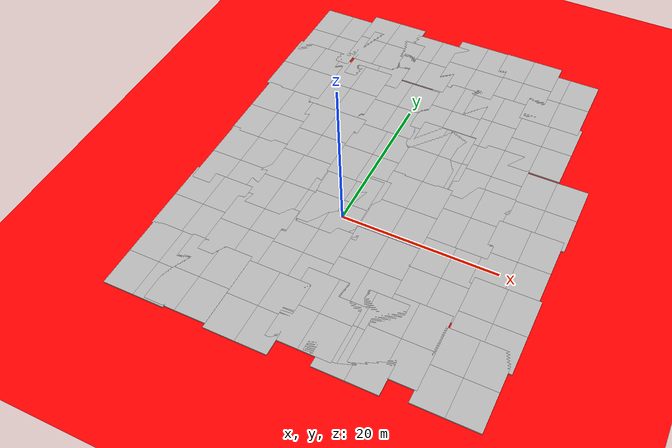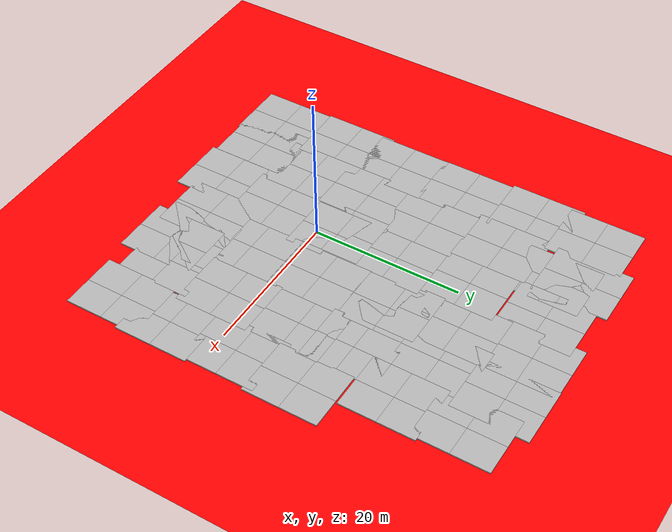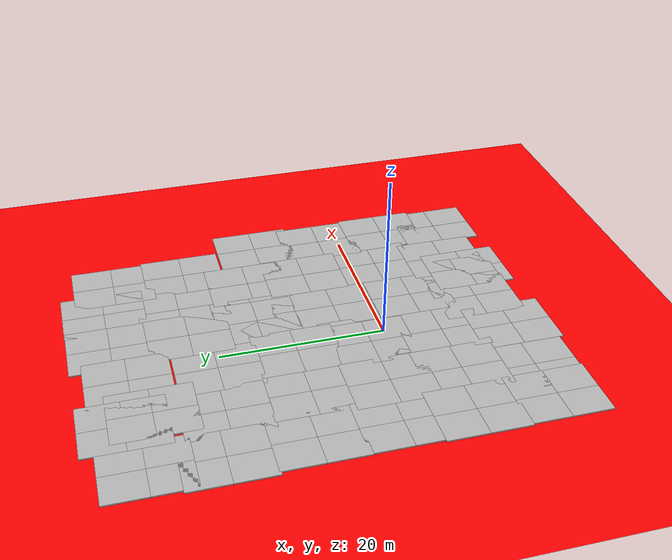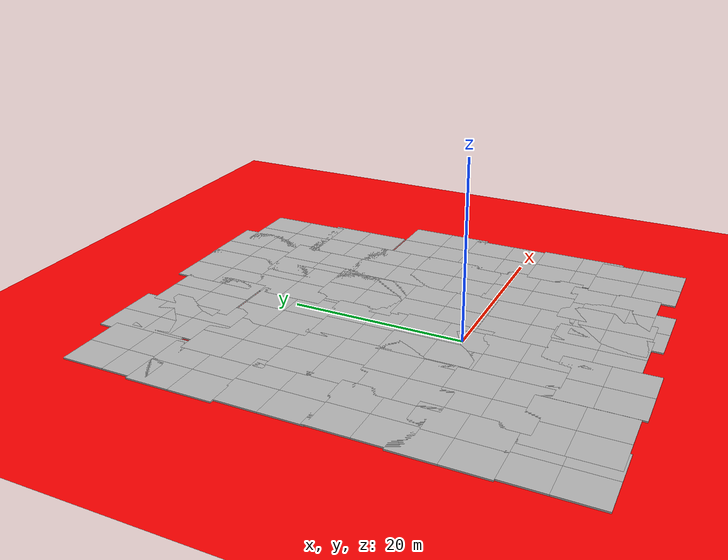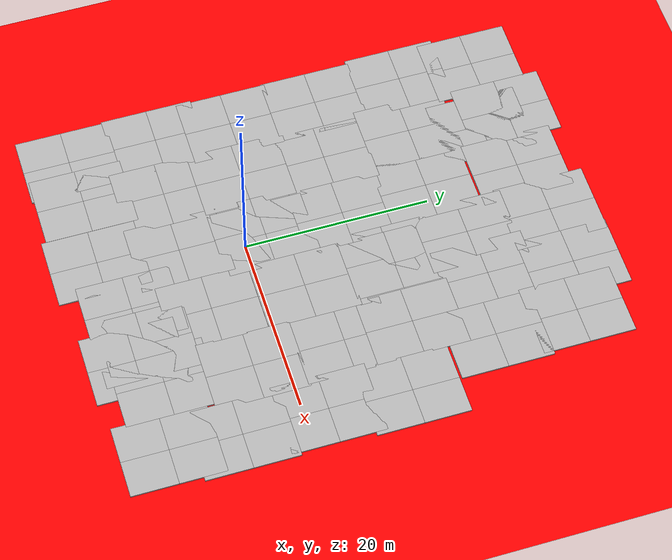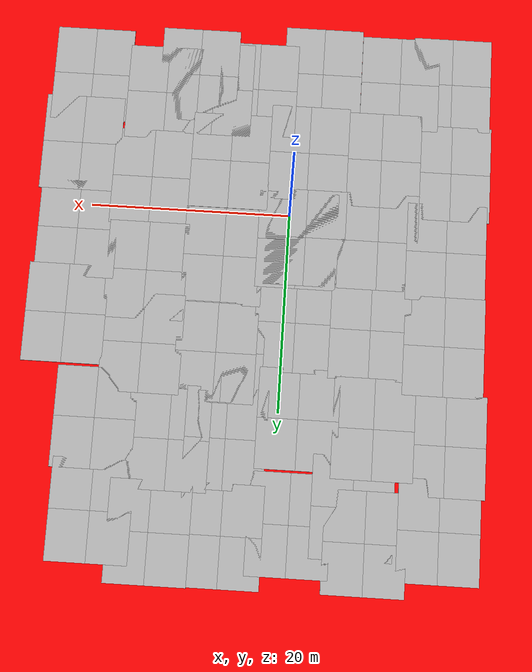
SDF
<sdf version="1.6">
 <world name="default">
  <model name="ground_plane">
   <static>1</static>
   <link name="link">
    <collision name="collision">
     <geometry><plane><normal>0 0 1</normal><size>100 100</size></plane></geometry>
     <surface><friction><ode><mu>100</mu><mu2>50</mu2></ode></friction></surface>
    </collision>
    <visual name="visual">
     <cast_shadows>0</cast_shadows>
     <geometry><plane><normal>0 0 1</normal><size>100 100</size></plane></geometry>
     <material>
      <ambient>1 0 0 1</ambient>
      <diffuse>1 0 0 1</diffuse>
      <specular>0.1 0.1 0.1 1</specular>
      <emissive>0 0 0 0</emissive>
     </material>
    </visual>
   </link>
  </model>
  <light name="sun" type="directional">
   <pose>0 0 10 0 -0 0</pose>
   <diffuse>0.8 0.8 0.8 1</diffuse>
   <specular>0.2 0.2 0.2 1</specular>
   <attenuation>
    <range>1000</range>
    <constant>0.9</constant>
    <linear>0.01</linear>
    <quadratic>0.001</quadratic>
   </attenuation>
   <direction>-0.5 0.1 -0.9</direction>
  </light>
  <gravity>0 0 -9.8</gravity>
  <magnetic_field>6e-06 2.3e-05 -4.2e-05</magnetic_field>
  <atmosphere type="adiabatic"/>
  <physics name="default_physics" default="0" type="ode">
   <max_step_size>0.001</max_step_size>
   <real_time_factor>1</real_time_factor>
   <real_time_update_rate>1000</real_time_update_rate>
  </physics>
  <scene><ambient>0.4 0.4 0.4 1</ambient><background>0.7 0.7 0.7 1</background><shadows>1</shadows></scene>
  <audio><device>default</device></audio>
  <spherical_coordinates>
   <surface_model>EARTH_WGS84</surface_model>
   <latitude_deg>0</latitude_deg>
   <longitude_deg>0</longitude_deg>
   <elevation>0</elevation>
   <heading_deg>0</heading_deg>
  </spherical_coordinates>
  <model name="mud_box">
   <static>1</static>
   <link name="link">
    <collision name="collision"><geometry><box><size>8 10 0.2</size></box></geometry></collision>
    <visual name="visual_1">
     <pose>-2 2.5 0 0 -0 0</pose>
     <cast_shadows>0</cast_shadows>
     <geometry><box><size>4 5 0.2</size></box></geometry>
     <material>
      <script>
       <uri>model://mud_box/materials/scripts</uri>
       <uri>model://mud_box/materials/textures</uri>
       <name>vrc/mud</name>
      </script>
     </material>
    </visual>
    <visual name="visual_2">
     <pose>2 2.5 0 0 -0 0</pose>
     <cast_shadows>0</cast_shadows>
     <geometry><box><size>4 5 0.2</size></box></geometry>
     <material>
      <script>
       <uri>model://mud_box/materials/scripts</uri>
       <uri>model://mud_box/materials/textures</uri>
       <name>vrc/mud</name>
      </script>
     </material>
    </visual>
    <visual name="visual_3">
     <pose>2 -2.5 0 0 -0 0</pose>
     <cast_shadows>0</cast_shadows>
     <geometry><box><size>4 5 0.2</size></box></geometry>
     <material>
      <script>
       <uri>model://mud_box/materials/scripts</uri>
       <uri>model://mud_box/materials/textures</uri>
       <name>vrc/mud</name>
      </script>
     </material>
    </visual>
    <visual name="visual_4">
     <pose>-2 -2.5 0 0 -0 0</pose>
     <cast_shadows>0</cast_shadows>
     <geometry><box><size>4 5 0.2</size></box></geometry>
     <material>
      <script>
       <uri>model://mud_box/materials/scripts</uri>
       <uri>model://mud_box/materials/textures</uri>
       <name>vrc/mud</name>
      </script>
     </material>
    </visual>
   </link>
   <pose>-9.02524 2.09965 0 0 -0 0</pose>
  </model>
  <model name="mud_box_clone">
   <static>1</static>
   <link name="link">
    <collision name="collision"><geometry><box><size>8 10 0.2</size></box></geometry></collision>
    <visual name="visual_1">
     <pose>-2 2.5 0 0 -0 0</pose>
     <cast_shadows>0</cast_shadows>
     <geometry><box><size>4 5 0.2</size></box></geometry>
     <material>
      <script>
       <uri>model://mud_box/materials/scripts</uri>
       <uri>model://mud_box/materials/textures</uri>
       <name>vrc/mud</name>
      </script>
     </material>
    </visual>
    <visual name="visual_2">
     <pose>2 2.5 0 0 -0 0</pose>
     <cast_shadows>0</cast_shadows>
     <geometry><box><size>4 5 0.2</size></box></geometry>
     <material>
      <script>
       <uri>model://mud_box/materials/scripts</uri>
       <uri>model://mud_box/materials/textures</uri>
       <name>vrc/mud</name>
      </script>
     </material>
    </visual>
    <visual name="visual_3">
     <pose>2 -2.5 0 0 -0 0</pose>
     <cast_shadows>0</cast_shadows>
     <geometry><box><size>4 5 0.2</size></box></geometry>
     <material>
      <script>
       <uri>model://mud_box/materials/scripts</uri>
       <uri>model://mud_box/materials/textures</uri>
       <name>vrc/mud</name>
      </script>
     </material>
    </visual>
    <visual name="visual_4">
     <pose>-2 -2.5 0 0 -0 0</pose>
     <cast_shadows>0</cast_shadows>
     <geometry><box><size>4 5 0.2</size></box></geometry>
     <material>
      <script>
       <uri>model://mud_box/materials/scripts</uri>
       <uri>model://mud_box/materials/textures</uri>
       <name>vrc/mud</name>
      </script>
     </material>
    </visual>
   </link>
   <pose>-9.01138 -6.47442 0 0 -0 0</pose>
  </model>
  <model name="mud_box_clone_0">
   <static>1</static>
   <link name="link">
    <collision name="collision"><geometry><box><size>8 10 0.2</size></box></geometry></collision>
    <visual name="visual_1">
     <pose>-2 2.5 0 0 -0 0</pose>
     <cast_shadows>0</cast_shadows>
     <geometry><box><size>4 5 0.2</size></box></geometry>
     <material>
      <script>
       <uri>model://mud_box/materials/scripts</uri>
       <uri>model://mud_box/materials/textures</uri>
       <name>vrc/mud</name>
      </script>
     </material>
    </visual>
    <visual name="visual_2">
     <pose>2 2.5 0 0 -0 0</pose>
     <cast_shadows>0</cast_shadows>
     <geometry><box><size>4 5 0.2</size></box></geometry>
     <material>
      <script>
       <uri>model://mud_box/materials/scripts</uri>
       <uri>model://mud_box/materials/textures</uri>
       <name>vrc/mud</name>
      </script>
     </material>
    </visual>
    <visual name="visual_3">
     <pose>2 -2.5 0 0 -0 0</pose>
     <cast_shadows>0</cast_shadows>
     <geometry><box><size>4 5 0.2</size></box></geometry>
     <material>
      <script>
       <uri>model://mud_box/materials/scripts</uri>
       <uri>model://mud_box/materials/textures</uri>
       <name>vrc/mud</name>
      </script>
     </material>
    </visual>
    <visual name="visual_4">
     <pose>-2 -2.5 0 0 -0 0</pose>
     <cast_shadows>0</cast_shadows>
     <geometry><box><size>4 5 0.2</size></box></geometry>
     <material>
      <script>
       <uri>model://mud_box/materials/scripts</uri>
       <uri>model://mud_box/materials/textures</uri>
       <name>vrc/mud</name>
      </script>
     </material>
    </visual>
   </link>
   <pose>-0.907816 2.44072 0 0 -0 0</pose>
  </model>
  <model name="mud_box_clone_1">
   <static>1</static>
   <link name="link">
    <collision name="collision"><geometry><box><size>8 10 0.2</size></box></geometry></collision>
    <visual name="visual_1">
     <pose>-2 2.5 0 0 -0 0</pose>
     <cast_shadows>0</cast_shadows>
     <geometry><box><size>4 5 0.2</size></box></geometry>
     <material>
      <script>
       <uri>model://mud_box/materials/scripts</uri>
       <uri>model://mud_box/materials/textures</uri>
       <name>vrc/mud</name>
      </script>
     </material>
    </visual>
    <visual name="visual_2">
     <pose>2 2.5 0 0 -0 0</pose>
     <cast_shadows>0</cast_shadows>
     <geometry><box><size>4 5 0.2</size></box></geometry>
     <material>
      <script>
       <uri>model://mud_box/materials/scripts</uri>
       <uri>model://mud_box/materials/textures</uri>
       <name>vrc/mud</name>
      </script>
     </material>
    </visual>
    <visual name="visual_3">
     <pose>2 -2.5 0 0 -0 0</pose>
     <cast_shadows>0</cast_shadows>
     <geometry><box><size>4 5 0.2</size></box></geometry>
     <material>
      <script>
       <uri>model://mud_box/materials/scripts</uri>
       <uri>model://mud_box/materials/textures</uri>
       <name>vrc/mud</name>
      </script>
     </material>
    </visual>
    <visual name="visual_4">
     <pose>-2 -2.5 0 0 -0 0</pose>
     <cast_shadows>0</cast_shadows>
     <geometry><box><size>4 5 0.2</size></box></geometry>
     <material>
      <script>
       <uri>model://mud_box/materials/scripts</uri>
       <uri>model://mud_box/materials/textures</uri>
       <name>vrc/mud</name>
      </script>
     </material>
    </visual>
   </link>
   <pose>-1.61149 -6.78882 0 0 -0 0</pose>
  </model>
  <model name="mud_box_clone_2">
   <static>1</static>
   <link name="link">
    <collision name="collision"><geometry><box><size>8 10 0.2</size></box></geometry></collision>
    <visual name="visual_1">
     <pose>-2 2.5 0 0 -0 0</pose>
     <cast_shadows>0</cast_shadows>
     <geometry><box><size>4 5 0.2</size></box></geometry>
     <material>
      <script>
       <uri>model://mud_box/materials/scripts</uri>
       <uri>model://mud_box/materials/textures</uri>
       <name>vrc/mud</name>
      </script>
     </material>
    </visual>
    <visual name="visual_2">
     <pose>2 2.5 0 0 -0 0</pose>
     <cast_shadows>0</cast_shadows>
     <geometry><box><size>4 5 0.2</size></box></geometry>
     <material>
      <script>
       <uri>model://mud_box/materials/scripts</uri>
       <uri>model://mud_box/materials/textures</uri>
       <name>vrc/mud</name>
      </script>
     </material>
    </visual>
    <visual name="visual_3">
     <pose>2 -2.5 0 0 -0 0</pose>
     <cast_shadows>0</cast_shadows>
     <geometry><box><size>4 5 0.2</size></box></geometry>
     <material>
      <script>
       <uri>model://mud_box/materials/scripts</uri>
       <uri>model://mud_box/materials/textures</uri>
       <name>vrc/mud</name>
      </script>
     </material>
    </visual>
    <visual name="visual_4">
     <pose>-2 -2.5 0 0 -0 0</pose>
     <cast_shadows>0</cast_shadows>
     <geometry><box><size>4 5 0.2</size></box></geometry>
     <material>
      <script>
       <uri>model://mud_box/materials/scripts</uri>
       <uri>model://mud_box/materials/textures</uri>
       <name>vrc/mud</name>
      </script>
     </material>
    </visual>
   </link>
   <pose>6.41573 4.52602 0 0 -0 0</pose>
  </model>
  <model name="mud_box_clone_3">
   <static>1</static>
   <link name="link">
    <collision name="collision"><geometry><box><size>8 10 0.2</size></box></geometry></collision>
    <visual name="visual_1">
     <pose>-2 2.5 0 0 -0 0</pose>
     <cast_shadows>0</cast_shadows>
     <geometry><box><size>4 5 0.2</size></box></geometry>
     <material>
      <script>
       <uri>model://mud_box/materials/scripts</uri>
       <uri>model://mud_box/materials/textures</uri>
       <name>vrc/mud</name>
      </script>
     </material>
    </visual>
    <visual name="visual_2">
     <pose>2 2.5 0 0 -0 0</pose>
     <cast_shadows>0</cast_shadows>
     <geometry><box><size>4 5 0.2</size></box></geometry>
     <material>
      <script>
       <uri>model://mud_box/materials/scripts</uri>
       <uri>model://mud_box/materials/textures</uri>
       <name>vrc/mud</name>
      </script>
     </material>
    </visual>
    <visual name="visual_3">
     <pose>2 -2.5 0 0 -0 0</pose>
     <cast_shadows>0</cast_shadows>
     <geometry><box><size>4 5 0.2</size></box></geometry>
     <material>
      <script>
       <uri>model://mud_box/materials/scripts</uri>
       <uri>model://mud_box/materials/textures</uri>
       <name>vrc/mud</name>
      </script>
     </material>
    </visual>
    <visual name="visual_4">
     <pose>-2 -2.5 0 0 -0 0</pose>
     <cast_shadows>0</cast_shadows>
     <geometry><box><size>4 5 0.2</size></box></geometry>
     <material>
      <script>
       <uri>model://mud_box/materials/scripts</uri>
       <uri>model://mud_box/materials/textures</uri>
       <name>vrc/mud</name>
      </script>
     </material>
    </visual>
   </link>
   <pose>6.33977 -5.49838 0 0 -0 0</pose>
  </model>
  <model name="mud_box_clone_4">
   <static>1</static>
   <link name="link">
    <collision name="collision"><geometry><box><size>8 10 0.2</size></box></geometry></collision>
    <visual name="visual_1">
     <pose>-2 2.5 0 0 -0 0</pose>
     <cast_shadows>0</cast_shadows>
     <geometry><box><size>4 5 0.2</size></box></geometry>
     <material>
      <script>
       <uri>model://mud_box/materials/scripts</uri>
       <uri>model://mud_box/materials/textures</uri>
       <name>vrc/mud</name>
      </script>
     </material>
    </visual>
    <visual name="visual_2">
     <pose>2 2.5 0 0 -0 0</pose>
     <cast_shadows>0</cast_shadows>
     <geometry><box><size>4 5 0.2</size></box></geometry>
     <material>
      <script>
       <uri>model://mud_box/materials/scripts</uri>
       <uri>model://mud_box/materials/textures</uri>
       <name>vrc/mud</name>
      </script>
     </material>
    </visual>
    <visual name="visual_3">
     <pose>2 -2.5 0 0 -0 0</pose>
     <cast_shadows>0</cast_shadows>
     <geometry><box><size>4 5 0.2</size></box></geometry>
     <material>
      <script>
       <uri>model://mud_box/materials/scripts</uri>
       <uri>model://mud_box/materials/textures</uri>
       <name>vrc/mud</name>
      </script>
     </material>
    </visual>
    <visual name="visual_4">
     <pose>-2 -2.5 0 0 -0 0</pose>
     <cast_shadows>0</cast_shadows>
     <geometry><box><size>4 5 0.2</size></box></geometry>
     <material>
      <script>
       <uri>model://mud_box/materials/scripts</uri>
       <uri>model://mud_box/materials/textures</uri>
       <name>vrc/mud</name>
      </script>
     </material>
    </visual>
   </link>
   <pose>13.9982 6.44176 0 0 -0 0</pose>
  </model>
  <model name="mud_box_clone_5">
   <static>1</static>
   <link name="link">
    <collision name="collision"><geometry><box><size>8 10 0.2</size></box></geometry></collision>
    <visual name="visual_1">
     <pose>-2 2.5 0 0 -0 0</pose>
     <cast_shadows>0</cast_shadows>
     <geometry><box><size>4 5 0.2</size></box></geometry>
     <material>
      <script>
       <uri>model://mud_box/materials/scripts</uri>
       <uri>model://mud_box/materials/textures</uri>
       <name>vrc/mud</name>
      </script>
     </material>
    </visual>
    <visual name="visual_2">
     <pose>2 2.5 0 0 -0 0</pose>
     <cast_shadows>0</cast_shadows>
     <geometry><box><size>4 5 0.2</size></box></geometry>
     <material>
      <script>
       <uri>model://mud_box/materials/scripts</uri>
       <uri>model://mud_box/materials/textures</uri>
       <name>vrc/mud</name>
      </script>
     </material>
    </visual>
    <visual name="visual_3">
     <pose>2 -2.5 0 0 -0 0</pose>
     <cast_shadows>0</cast_shadows>
     <geometry><box><size>4 5 0.2</size></box></geometry>
     <material>
      <script>
       <uri>model://mud_box/materials/scripts</uri>
       <uri>model://mud_box/materials/textures</uri>
       <name>vrc/mud</name>
      </script>
     </material>
    </visual>
    <visual name="visual_4">
     <pose>-2 -2.5 0 0 -0 0</pose>
     <cast_shadows>0</cast_shadows>
     <geometry><box><size>4 5 0.2</size></box></geometry>
     <material>
      <script>
       <uri>model://mud_box/materials/scripts</uri>
       <uri>model://mud_box/materials/textures</uri>
       <name>vrc/mud</name>
      </script>
     </material>
    </visual>
   </link>
   <pose>14.1998 -3.30517 0 0 -0 0</pose>
  </model>
  <model name="mud_box_clone_6">
   <static>1</static>
   <link name="link">
    <collision name="collision"><geometry><box><size>8 10 0.2</size></box></geometry></collision>
    <visual name="visual_1">
     <pose>-2 2.5 0 0 -0 0</pose>
     <cast_shadows>0</cast_shadows>
     <geometry><box><size>4 5 0.2</size></box></geometry>
     <material>
      <script>
       <uri>model://mud_box/materials/scripts</uri>
       <uri>model://mud_box/materials/textures</uri>
       <name>vrc/mud</name>
      </script>
     </material>
    </visual>
    <visual name="visual_2">
     <pose>2 2.5 0 0 -0 0</pose>
     <cast_shadows>0</cast_shadows>
     <geometry><box><size>4 5 0.2</size></box></geometry>
     <material>
      <script>
       <uri>model://mud_box/materials/scripts</uri>
       <uri>model://mud_box/materials/textures</uri>
       <name>vrc/mud</name>
      </script>
     </material>
    </visual>
    <visual name="visual_3">
     <pose>2 -2.5 0 0 -0 0</pose>
     <cast_shadows>0</cast_shadows>
     <geometry><box><size>4 5 0.2</size></box></geometry>
     <material>
      <script>
       <uri>model://mud_box/materials/scripts</uri>
       <uri>model://mud_box/materials/textures</uri>
       <name>vrc/mud</name>
      </script>
     </material>
    </visual>
    <visual name="visual_4">
     <pose>-2 -2.5 0 0 -0 0</pose>
     <cast_shadows>0</cast_shadows>
     <geometry><box><size>4 5 0.2</size></box></geometry>
     <material>
      <script>
       <uri>model://mud_box/materials/scripts</uri>
       <uri>model://mud_box/materials/textures</uri>
       <name>vrc/mud</name>
      </script>
     </material>
    </visual>
   </link>
   <pose>13.4278 -12.4629 0 0 -0 0</pose>
  </model>
  <model name="mud_box_clone_7">
   <static>1</static>
   <link name="link">
    <collision name="collision"><geometry><box><size>8 10 0.2</size></box></geometry></collision>
    <visual name="visual_1">
     <pose>-2 2.5 0 0 -0 0</pose>
     <cast_shadows>0</cast_shadows>
     <geometry><box><size>4 5 0.2</size></box></geometry>
     <material>
      <script>
       <uri>model://mud_box/materials/scripts</uri>
       <uri>model://mud_box/materials/textures</uri>
       <name>vrc/mud</name>
      </script>
     </material>
    </visual>
    <visual name="visual_2">
     <pose>2 2.5 0 0 -0 0</pose>
     <cast_shadows>0</cast_shadows>
     <geometry><box><size>4 5 0.2</size></box></geometry>
     <material>
      <script>
       <uri>model://mud_box/materials/scripts</uri>
       <uri>model://mud_box/materials/textures</uri>
       <name>vrc/mud</name>
      </script>
     </material>
    </visual>
    <visual name="visual_3">
     <pose>2 -2.5 0 0 -0 0</pose>
     <cast_shadows>0</cast_shadows>
     <geometry><box><size>4 5 0.2</size></box></geometry>
     <material>
      <script>
       <uri>model://mud_box/materials/scripts</uri>
       <uri>model://mud_box/materials/textures</uri>
       <name>vrc/mud</name>
      </script>
     </material>
    </visual>
    <visual name="visual_4">
     <pose>-2 -2.5 0 0 -0 0</pose>
     <cast_shadows>0</cast_shadows>
     <geometry><box><size>4 5 0.2</size></box></geometry>
     <material>
      <script>
       <uri>model://mud_box/materials/scripts</uri>
       <uri>model://mud_box/materials/textures</uri>
       <name>vrc/mud</name>
      </script>
     </material>
    </visual>
   </link>
   <pose>3.9904 -13.3757 0 0 -0 0</pose>
  </model>
  <model name="mud_box_clone_8">
   <static>1</static>
   <link name="link">
    <collision name="collision"><geometry><box><size>8 10 0.2</size></box></geometry></collision>
    <visual name="visual_1">
     <pose>-2 2.5 0 0 -0 0</pose>
     <cast_shadows>0</cast_shadows>
     <geometry><box><size>4 5 0.2</size></box></geometry>
     <material>
      <script>
       <uri>model://mud_box/materials/scripts</uri>
       <uri>model://mud_box/materials/textures</uri>
       <name>vrc/mud</name>
      </script>
     </material>
    </visual>
    <visual name="visual_2">
     <pose>2 2.5 0 0 -0 0</pose>
     <cast_shadows>0</cast_shadows>
     <geometry><box><size>4 5 0.2</size></box></geometry>
     <material>
      <script>
       <uri>model://mud_box/materials/scripts</uri>
       <uri>model://mud_box/materials/textures</uri>
       <name>vrc/mud</name>
      </script>
     </material>
    </visual>
    <visual name="visual_3">
     <pose>2 -2.5 0 0 -0 0</pose>
     <cast_shadows>0</cast_shadows>
     <geometry><box><size>4 5 0.2</size></box></geometry>
     <material>
      <script>
       <uri>model://mud_box/materials/scripts</uri>
       <uri>model://mud_box/materials/textures</uri>
       <name>vrc/mud</name>
      </script>
     </material>
    </visual>
    <visual name="visual_4">
     <pose>-2 -2.5 0 0 -0 0</pose>
     <cast_shadows>0</cast_shadows>
     <geometry><box><size>4 5 0.2</size></box></geometry>
     <material>
      <script>
       <uri>model://mud_box/materials/scripts</uri>
       <uri>model://mud_box/materials/textures</uri>
       <name>vrc/mud</name>
      </script>
     </material>
    </visual>
   </link>
   <pose>8.56451 -13.1819 0 0 -0 0</pose>
  </model>
  <model name="mud_box_clone_9">
   <static>1</static>
   <link name="link">
    <collision name="collision"><geometry><box><size>8 10 0.2</size></box></geometry></collision>
    <visual name="visual_1">
     <pose>-2 2.5 0 0 -0 0</pose>
     <cast_shadows>0</cast_shadows>
     <geometry><box><size>4 5 0.2</size></box></geometry>
     <material>
      <script>
       <uri>model://mud_box/materials/scripts</uri>
       <uri>model://mud_box/materials/textures</uri>
       <name>vrc/mud</name>
      </script>
     </material>
    </visual>
    <visual name="visual_2">
     <pose>2 2.5 0 0 -0 0</pose>
     <cast_shadows>0</cast_shadows>
     <geometry><box><size>4 5 0.2</size></box></geometry>
     <material>
      <script>
       <uri>model://mud_box/materials/scripts</uri>
       <uri>model://mud_box/materials/textures</uri>
       <name>vrc/mud</name>
      </script>
     </material>
    </visual>
    <visual name="visual_3">
     <pose>2 -2.5 0 0 -0 0</pose>
     <cast_shadows>0</cast_shadows>
     <geometry><box><size>4 5 0.2</size></box></geometry>
     <material>
      <script>
       <uri>model://mud_box/materials/scripts</uri>
       <uri>model://mud_box/materials/textures</uri>
       <name>vrc/mud</name>
      </script>
     </material>
    </visual>
    <visual name="visual_4">
     <pose>-2 -2.5 0 0 -0 0</pose>
     <cast_shadows>0</cast_shadows>
     <geometry><box><size>4 5 0.2</size></box></geometry>
     <material>
      <script>
       <uri>model://mud_box/materials/scripts</uri>
       <uri>model://mud_box/materials/textures</uri>
       <name>vrc/mud</name>
      </script>
     </material>
    </visual>
   </link>
   <pose>-2.58874 -15.4114 0 0 -0 0</pose>
  </model>
  <model name="mud_box_clone_10">
   <static>1</static>
   <link name="link">
    <collision name="collision"><geometry><box><size>8 10 0.2</size></box></geometry></collision>
    <visual name="visual_1">
     <pose>-2 2.5 0 0 -0 0</pose>
     <cast_shadows>0</cast_shadows>
     <geometry><box><size>4 5 0.2</size></box></geometry>
     <material>
      <script>
       <uri>model://mud_box/materials/scripts</uri>
       <uri>model://mud_box/materials/textures</uri>
       <name>vrc/mud</name>
      </script>
     </material>
    </visual>
    <visual name="visual_2">
     <pose>2 2.5 0 0 -0 0</pose>
     <cast_shadows>0</cast_shadows>
     <geometry><box><size>4 5 0.2</size></box></geometry>
     <material>
      <script>
       <uri>model://mud_box/materials/scripts</uri>
       <uri>model://mud_box/materials/textures</uri>
       <name>vrc/mud</name>
      </script>
     </material>
    </visual>
    <visual name="visual_3">
     <pose>2 -2.5 0 0 -0 0</pose>
     <cast_shadows>0</cast_shadows>
     <geometry><box><size>4 5 0.2</size></box></geometry>
     <material>
      <script>
       <uri>model://mud_box/materials/scripts</uri>
       <uri>model://mud_box/materials/textures</uri>
       <name>vrc/mud</name>
      </script>
     </material>
    </visual>
    <visual name="visual_4">
     <pose>-2 -2.5 0 0 -0 0</pose>
     <cast_shadows>0</cast_shadows>
     <geometry><box><size>4 5 0.2</size></box></geometry>
     <material>
      <script>
       <uri>model://mud_box/materials/scripts</uri>
       <uri>model://mud_box/materials/textures</uri>
       <name>vrc/mud</name>
      </script>
     </material>
    </visual>
   </link>
   <pose>-10.6003 -14.8746 0 0 -0 0</pose>
  </model>
  <model name="mud_box_clone_11">
   <static>1</static>
   <link name="link">
    <collision name="collision"><geometry><box><size>8 10 0.2</size></box></geometry></collision>
    <visual name="visual_1">
     <pose>-2 2.5 0 0 -0 0</pose>
     <cast_shadows>0</cast_shadows>
     <geometry><box><size>4 5 0.2</size></box></geometry>
     <material>
      <script>
       <uri>model://mud_box/materials/scripts</uri>
       <uri>model://mud_box/materials/textures</uri>
       <name>vrc/mud</name>
      </script>
     </material>
    </visual>
    <visual name="visual_2">
     <pose>2 2.5 0 0 -0 0</pose>
     <cast_shadows>0</cast_shadows>
     <geometry><box><size>4 5 0.2</size></box></geometry>
     <material>
      <script>
       <uri>model://mud_box/materials/scripts</uri>
       <uri>model://mud_box/materials/textures</uri>
       <name>vrc/mud</name>
      </script>
     </material>
    </visual>
    <visual name="visual_3">
     <pose>2 -2.5 0 0 -0 0</pose>
     <cast_shadows>0</cast_shadows>
     <geometry><box><size>4 5 0.2</size></box></geometry>
     <material>
      <script>
       <uri>model://mud_box/materials/scripts</uri>
       <uri>model://mud_box/materials/textures</uri>
       <name>vrc/mud</name>
      </script>
     </material>
    </visual>
    <visual name="visual_4">
     <pose>-2 -2.5 0 0 -0 0</pose>
     <cast_shadows>0</cast_shadows>
     <geometry><box><size>4 5 0.2</size></box></geometry>
     <material>
      <script>
       <uri>model://mud_box/materials/scripts</uri>
       <uri>model://mud_box/materials/textures</uri>
       <name>vrc/mud</name>
      </script>
     </material>
    </visual>
   </link>
   <pose>-16.1399 -5.49382 0 0 -0 0</pose>
  </model>
  <model name="mud_box_clone_12">
   <static>1</static>
   <link name="link">
    <collision name="collision"><geometry><box><size>8 10 0.2</size></box></geometry></collision>
    <visual name="visual_1">
     <pose>-2 2.5 0 0 -0 0</pose>
     <cast_shadows>0</cast_shadows>
     <geometry><box><size>4 5 0.2</size></box></geometry>
     <material>
      <script>
       <uri>model://mud_box/materials/scripts</uri>
       <uri>model://mud_box/materials/textures</uri>
       <name>vrc/mud</name>
      </script>
     </material>
    </visual>
    <visual name="visual_2">
     <pose>2 2.5 0 0 -0 0</pose>
     <cast_shadows>0</cast_shadows>
     <geometry><box><size>4 5 0.2</size></box></geometry>
     <material>
      <script>
       <uri>model://mud_box/materials/scripts</uri>
       <uri>model://mud_box/materials/textures</uri>
       <name>vrc/mud</name>
      </script>
     </material>
    </visual>
    <visual name="visual_3">
     <pose>2 -2.5 0 0 -0 0</pose>
     <cast_shadows>0</cast_shadows>
     <geometry><box><size>4 5 0.2</size></box></geometry>
     <material>
      <script>
       <uri>model://mud_box/materials/scripts</uri>
       <uri>model://mud_box/materials/textures</uri>
       <name>vrc/mud</name>
      </script>
     </material>
    </visual>
    <visual name="visual_4">
     <pose>-2 -2.5 0 0 -0 0</pose>
     <cast_shadows>0</cast_shadows>
     <geometry><box><size>4 5 0.2</size></box></geometry>
     <material>
      <script>
       <uri>model://mud_box/materials/scripts</uri>
       <uri>model://mud_box/materials/textures</uri>
       <name>vrc/mud</name>
      </script>
     </material>
    </visual>
   </link>
   <pose>-15.9101 2.82816 0 0 -0 0</pose>
  </model>
  <model name="mud_box_clone_13">
   <static>1</static>
   <link name="link">
    <collision name="collision"><geometry><box><size>8 10 0.2</size></box></geometry></collision>
    <visual name="visual_1">
     <pose>-2 2.5 0 0 -0 0</pose>
     <cast_shadows>0</cast_shadows>
     <geometry><box><size>4 5 0.2</size></box></geometry>
     <material>
      <script>
       <uri>model://mud_box/materials/scripts</uri>
       <uri>model://mud_box/materials/textures</uri>
       <name>vrc/mud</name>
      </script>
     </material>
    </visual>
    <visual name="visual_2">
     <pose>2 2.5 0 0 -0 0</pose>
     <cast_shadows>0</cast_shadows>
     <geometry><box><size>4 5 0.2</size></box></geometry>
     <material>
      <script>
       <uri>model://mud_box/materials/scripts</uri>
       <uri>model://mud_box/materials/textures</uri>
       <name>vrc/mud</name>
      </script>
     </material>
    </visual>
    <visual name="visual_3">
     <pose>2 -2.5 0 0 -0 0</pose>
     <cast_shadows>0</cast_shadows>
     <geometry><box><size>4 5 0.2</size></box></geometry>
     <material>
      <script>
       <uri>model://mud_box/materials/scripts</uri>
       <uri>model://mud_box/materials/textures</uri>
       <name>vrc/mud</name>
      </script>
     </material>
    </visual>
    <visual name="visual_4">
     <pose>-2 -2.5 0 0 -0 0</pose>
     <cast_shadows>0</cast_shadows>
     <geometry><box><size>4 5 0.2</size></box></geometry>
     <material>
      <script>
       <uri>model://mud_box/materials/scripts</uri>
       <uri>model://mud_box/materials/textures</uri>
       <name>vrc/mud</name>
      </script>
     </material>
    </visual>
   </link>
   <pose>-15.9438 -15.0899 0 0 -0 0</pose>
  </model>
  <model name="mud_box_clone_14">
   <static>1</static>
   <link name="link">
    <collision name="collision"><geometry><box><size>8 10 0.2</size></box></geometry></collision>
    <visual name="visual_1">
     <pose>-2 2.5 0 0 -0 0</pose>
     <cast_shadows>0</cast_shadows>
     <geometry><box><size>4 5 0.2</size></box></geometry>
     <material>
      <script>
       <uri>model://mud_box/materials/scripts</uri>
       <uri>model://mud_box/materials/textures</uri>
       <name>vrc/mud</name>
      </script>
     </material>
    </visual>
    <visual name="visual_2">
     <pose>2 2.5 0 0 -0 0</pose>
     <cast_shadows>0</cast_shadows>
     <geometry><box><size>4 5 0.2</size></box></geometry>
     <material>
      <script>
       <uri>model://mud_box/materials/scripts</uri>
       <uri>model://mud_box/materials/textures</uri>
       <name>vrc/mud</name>
      </script>
     </material>
    </visual>
    <visual name="visual_3">
     <pose>2 -2.5 0 0 -0 0</pose>
     <cast_shadows>0</cast_shadows>
     <geometry><box><size>4 5 0.2</size></box></geometry>
     <material>
      <script>
       <uri>model://mud_box/materials/scripts</uri>
       <uri>model://mud_box/materials/textures</uri>
       <name>vrc/mud</name>
      </script>
     </material>
    </visual>
    <visual name="visual_4">
     <pose>-2 -2.5 0 0 -0 0</pose>
     <cast_shadows>0</cast_shadows>
     <geometry><box><size>4 5 0.2</size></box></geometry>
     <material>
      <script>
       <uri>model://mud_box/materials/scripts</uri>
       <uri>model://mud_box/materials/textures</uri>
       <name>vrc/mud</name>
      </script>
     </material>
    </visual>
   </link>
   <pose>13.8616 13.8293 0 0 -0 0</pose>
  </model>
  <model name="mud_box_clone_15">
   <static>1</static>
   <link name="link">
    <collision name="collision"><geometry><box><size>8 10 0.2</size></box></geometry></collision>
    <visual name="visual_1">
     <pose>-2 2.5 0 0 -0 0</pose>
     <cast_shadows>0</cast_shadows>
     <geometry><box><size>4 5 0.2</size></box></geometry>
     <material>
      <script>
       <uri>model://mud_box/materials/scripts</uri>
       <uri>model://mud_box/materials/textures</uri>
       <name>vrc/mud</name>
      </script>
     </material>
    </visual>
    <visual name="visual_2">
     <pose>2 2.5 0 0 -0 0</pose>
     <cast_shadows>0</cast_shadows>
     <geometry><box><size>4 5 0.2</size></box></geometry>
     <material>
      <script>
       <uri>model://mud_box/materials/scripts</uri>
       <uri>model://mud_box/materials/textures</uri>
       <name>vrc/mud</name>
      </script>
     </material>
    </visual>
    <visual name="visual_3">
     <pose>2 -2.5 0 0 -0 0</pose>
     <cast_shadows>0</cast_shadows>
     <geometry><box><size>4 5 0.2</size></box></geometry>
     <material>
      <script>
       <uri>model://mud_box/materials/scripts</uri>
       <uri>model://mud_box/materials/textures</uri>
       <name>vrc/mud</name>
      </script>
     </material>
    </visual>
    <visual name="visual_4">
     <pose>-2 -2.5 0 0 -0 0</pose>
     <cast_shadows>0</cast_shadows>
     <geometry><box><size>4 5 0.2</size></box></geometry>
     <material>
      <script>
       <uri>model://mud_box/materials/scripts</uri>
       <uri>model://mud_box/materials/textures</uri>
       <name>vrc/mud</name>
      </script>
     </material>
    </visual>
   </link>
   <pose>5.74694 14.2584 0 0 -0 0</pose>
  </model>
  <model name="mud_box_clone_16">
   <static>1</static>
   <link name="link">
    <collision name="collision"><geometry><box><size>8 10 0.2</size></box></geometry></collision>
    <visual name="visual_1">
     <pose>-2 2.5 0 0 -0 0</pose>
     <cast_shadows>0</cast_shadows>
     <geometry><box><size>4 5 0.2</size></box></geometry>
     <material>
      <script>
       <uri>model://mud_box/materials/scripts</uri>
       <uri>model://mud_box/materials/textures</uri>
       <name>vrc/mud</name>
      </script>
     </material>
    </visual>
    <visual name="visual_2">
     <pose>2 2.5 0 0 -0 0</pose>
     <cast_shadows>0</cast_shadows>
     <geometry><box><size>4 5 0.2</size></box></geometry>
     <material>
      <script>
       <uri>model://mud_box/materials/scripts</uri>
       <uri>model://mud_box/materials/textures</uri>
       <name>vrc/mud</name>
      </script>
     </material>
    </visual>
    <visual name="visual_3">
     <pose>2 -2.5 0 0 -0 0</pose>
     <cast_shadows>0</cast_shadows>
     <geometry><box><size>4 5 0.2</size></box></geometry>
     <material>
      <script>
       <uri>model://mud_box/materials/scripts</uri>
       <uri>model://mud_box/materials/textures</uri>
       <name>vrc/mud</name>
      </script>
     </material>
    </visual>
    <visual name="visual_4">
     <pose>-2 -2.5 0 0 -0 0</pose>
     <cast_shadows>0</cast_shadows>
     <geometry><box><size>4 5 0.2</size></box></geometry>
     <material>
      <script>
       <uri>model://mud_box/materials/scripts</uri>
       <uri>model://mud_box/materials/textures</uri>
       <name>vrc/mud</name>
      </script>
     </material>
    </visual>
   </link>
   <pose>6.48316 14.3508 0 0 -0 0</pose>
  </model>
  <model name="mud_box_clone_17">
   <static>1</static>
   <link name="link">
    <collision name="collision"><geometry><box><size>8 10 0.2</size></box></geometry></collision>
    <visual name="visual_1">
     <pose>-2 2.5 0 0 -0 0</pose>
     <cast_shadows>0</cast_shadows>
     <geometry><box><size>4 5 0.2</size></box></geometry>
     <material>
      <script>
       <uri>model://mud_box/materials/scripts</uri>
       <uri>model://mud_box/materials/textures</uri>
       <name>vrc/mud</name>
      </script>
     </material>
    </visual>
    <visual name="visual_2">
     <pose>2 2.5 0 0 -0 0</pose>
     <cast_shadows>0</cast_shadows>
     <geometry><box><size>4 5 0.2</size></box></geometry>
     <material>
      <script>
       <uri>model://mud_box/materials/scripts</uri>
       <uri>model://mud_box/materials/textures</uri>
       <name>vrc/mud</name>
      </script>
     </material>
    </visual>
    <visual name="visual_3">
     <pose>2 -2.5 0 0 -0 0</pose>
     <cast_shadows>0</cast_shadows>
     <geometry><box><size>4 5 0.2</size></box></geometry>
     <material>
      <script>
       <uri>model://mud_box/materials/scripts</uri>
       <uri>model://mud_box/materials/textures</uri>
       <name>vrc/mud</name>
      </script>
     </material>
    </visual>
    <visual name="visual_4">
     <pose>-2 -2.5 0 0 -0 0</pose>
     <cast_shadows>0</cast_shadows>
     <geometry><box><size>4 5 0.2</size></box></geometry>
     <material>
      <script>
       <uri>model://mud_box/materials/scripts</uri>
       <uri>model://mud_box/materials/textures</uri>
       <name>vrc/mud</name>
      </script>
     </material>
    </visual>
   </link>
   <pose>-1.17694 10.9468 0 0 -0 0</pose>
  </model>
  <model name="mud_box_clone_18">
   <static>1</static>
   <link name="link">
    <collision name="collision"><geometry><box><size>8 10 0.2</size></box></geometry></collision>
    <visual name="visual_1">
     <pose>-2 2.5 0 0 -0 0</pose>
     <cast_shadows>0</cast_shadows>
     <geometry><box><size>4 5 0.2</size></box></geometry>
     <material>
      <script>
       <uri>model://mud_box/materials/scripts</uri>
       <uri>model://mud_box/materials/textures</uri>
       <name>vrc/mud</name>
      </script>
     </material>
    </visual>
    <visual name="visual_2">
     <pose>2 2.5 0 0 -0 0</pose>
     <cast_shadows>0</cast_shadows>
     <geometry><box><size>4 5 0.2</size></box></geometry>
     <material>
      <script>
       <uri>model://mud_box/materials/scripts</uri>
       <uri>model://mud_box/materials/textures</uri>
       <name>vrc/mud</name>
      </script>
     </material>
    </visual>
    <visual name="visual_3">
     <pose>2 -2.5 0 0 -0 0</pose>
     <cast_shadows>0</cast_shadows>
     <geometry><box><size>4 5 0.2</size></box></geometry>
     <material>
      <script>
       <uri>model://mud_box/materials/scripts</uri>
       <uri>model://mud_box/materials/textures</uri>
       <name>vrc/mud</name>
      </script>
     </material>
    </visual>
    <visual name="visual_4">
     <pose>-2 -2.5 0 0 -0 0</pose>
     <cast_shadows>0</cast_shadows>
     <geometry><box><size>4 5 0.2</size></box></geometry>
     <material>
      <script>
       <uri>model://mud_box/materials/scripts</uri>
       <uri>model://mud_box/materials/textures</uri>
       <name>vrc/mud</name>
      </script>
     </material>
    </visual>
   </link>
   <pose>-8.65486 11.2273 0 0 -0 0</pose>
  </model>
  <model name="mud_box_clone_19">
   <static>1</static>
   <link name="link">
    <collision name="collision"><geometry><box><size>8 10 0.2</size></box></geometry></collision>
    <visual name="visual_1">
     <pose>-2 2.5 0 0 -0 0</pose>
     <cast_shadows>0</cast_shadows>
     <geometry><box><size>4 5 0.2</size></box></geometry>
     <material>
      <script>
       <uri>model://mud_box/materials/scripts</uri>
       <uri>model://mud_box/materials/textures</uri>
       <name>vrc/mud</name>
      </script>
     </material>
    </visual>
    <visual name="visual_2">
     <pose>2 2.5 0 0 -0 0</pose>
     <cast_shadows>0</cast_shadows>
     <geometry><box><size>4 5 0.2</size></box></geometry>
     <material>
      <script>
       <uri>model://mud_box/materials/scripts</uri>
       <uri>model://mud_box/materials/textures</uri>
       <name>vrc/mud</name>
      </script>
     </material>
    </visual>
    <visual name="visual_3">
     <pose>2 -2.5 0 0 -0 0</pose>
     <cast_shadows>0</cast_shadows>
     <geometry><box><size>4 5 0.2</size></box></geometry>
     <material>
      <script>
       <uri>model://mud_box/materials/scripts</uri>
       <uri>model://mud_box/materials/textures</uri>
       <name>vrc/mud</name>
      </script>
     </material>
    </visual>
    <visual name="visual_4">
     <pose>-2 -2.5 0 0 -0 0</pose>
     <cast_shadows>0</cast_shadows>
     <geometry><box><size>4 5 0.2</size></box></geometry>
     <material>
      <script>
       <uri>model://mud_box/materials/scripts</uri>
       <uri>model://mud_box/materials/textures</uri>
       <name>vrc/mud</name>
      </script>
     </material>
    </visual>
   </link>
   <pose>-16 12.4301 0 0 -0 0</pose>
  </model>
  <model name="mud_box_clone_20">
   <static>1</static>
   <link name="link">
    <collision name="collision"><geometry><box><size>8 10 0.2</size></box></geometry></collision>
    <visual name="visual_1">
     <pose>-2 2.5 0 0 -0 0</pose>
     <cast_shadows>0</cast_shadows>
     <geometry><box><size>4 5 0.2</size></box></geometry>
     <material>
      <script>
       <uri>model://mud_box/materials/scripts</uri>
       <uri>model://mud_box/materials/textures</uri>
       <name>vrc/mud</name>
      </script>
     </material>
    </visual>
    <visual name="visual_2">
     <pose>2 2.5 0 0 -0 0</pose>
     <cast_shadows>0</cast_shadows>
     <geometry><box><size>4 5 0.2</size></box></geometry>
     <material>
      <script>
       <uri>model://mud_box/materials/scripts</uri>
       <uri>model://mud_box/materials/textures</uri>
       <name>vrc/mud</name>
      </script>
     </material>
    </visual>
    <visual name="visual_3">
     <pose>2 -2.5 0 0 -0 0</pose>
     <cast_shadows>0</cast_shadows>
     <geometry><box><size>4 5 0.2</size></box></geometry>
     <material>
      <script>
       <uri>model://mud_box/materials/scripts</uri>
       <uri>model://mud_box/materials/textures</uri>
       <name>vrc/mud</name>
      </script>
     </material>
    </visual>
    <visual name="visual_4">
     <pose>-2 -2.5 0 0 -0 0</pose>
     <cast_shadows>0</cast_shadows>
     <geometry><box><size>4 5 0.2</size></box></geometry>
     <material>
      <script>
       <uri>model://mud_box/materials/scripts</uri>
       <uri>model://mud_box/materials/textures</uri>
       <name>vrc/mud</name>
      </script>
     </material>
    </visual>
   </link>
   <pose>-1.98322 20.4975 0 0 -0 0</pose>
  </model>
  <model name="mud_box_clone_21">
   <static>1</static>
   <link name="link">
    <collision name="collision"><geometry><box><size>8 10 0.2</size></box></geometry></collision>
    <visual name="visual_1">
     <pose>-2 2.5 0 0 -0 0</pose>
     <cast_shadows>0</cast_shadows>
     <geometry><box><size>4 5 0.2</size></box></geometry>
     <material>
      <script>
       <uri>model://mud_box/materials/scripts</uri>
       <uri>model://mud_box/materials/textures</uri>
       <name>vrc/mud</name>
      </script>
     </material>
    </visual>
    <visual name="visual_2">
     <pose>2 2.5 0 0 -0 0</pose>
     <cast_shadows>0</cast_shadows>
     <geometry><box><size>4 5 0.2</size></box></geometry>
     <material>
      <script>
       <uri>model://mud_box/materials/scripts</uri>
       <uri>model://mud_box/materials/textures</uri>
       <name>vrc/mud</name>
      </script>
     </material>
    </visual>
    <visual name="visual_3">
     <pose>2 -2.5 0 0 -0 0</pose>
     <cast_shadows>0</cast_shadows>
     <geometry><box><size>4 5 0.2</size></box></geometry>
     <material>
      <script>
       <uri>model://mud_box/materials/scripts</uri>
       <uri>model://mud_box/materials/textures</uri>
       <name>vrc/mud</name>
      </script>
     </material>
    </visual>
    <visual name="visual_4">
     <pose>-2 -2.5 0 0 -0 0</pose>
     <cast_shadows>0</cast_shadows>
     <geometry><box><size>4 5 0.2</size></box></geometry>
     <material>
      <script>
       <uri>model://mud_box/materials/scripts</uri>
       <uri>model://mud_box/materials/textures</uri>
       <name>vrc/mud</name>
      </script>
     </material>
    </visual>
   </link>
   <pose>-9.39199 21.0113 0 0 -0 0</pose>
  </model>
  <model name="mud_box_clone_22">
   <static>1</static>
   <link name="link">
    <collision name="collision"><geometry><box><size>8 10 0.2</size></box></geometry></collision>
    <visual name="visual_1">
     <pose>-2 2.5 0 0 -0 0</pose>
     <cast_shadows>0</cast_shadows>
     <geometry><box><size>4 5 0.2</size></box></geometry>
     <material>
      <script>
       <uri>model://mud_box/materials/scripts</uri>
       <uri>model://mud_box/materials/textures</uri>
       <name>vrc/mud</name>
      </script>
     </material>
    </visual>
    <visual name="visual_2">
     <pose>2 2.5 0 0 -0 0</pose>
     <cast_shadows>0</cast_shadows>
     <geometry><box><size>4 5 0.2</size></box></geometry>
     <material>
      <script>
       <uri>model://mud_box/materials/scripts</uri>
       <uri>model://mud_box/materials/textures</uri>
       <name>vrc/mud</name>
      </script>
     </material>
    </visual>
    <visual name="visual_3">
     <pose>2 -2.5 0 0 -0 0</pose>
     <cast_shadows>0</cast_shadows>
     <geometry><box><size>4 5 0.2</size></box></geometry>
     <material>
      <script>
       <uri>model://mud_box/materials/scripts</uri>
       <uri>model://mud_box/materials/textures</uri>
       <name>vrc/mud</name>
      </script>
     </material>
    </visual>
    <visual name="visual_4">
     <pose>-2 -2.5 0 0 -0 0</pose>
     <cast_shadows>0</cast_shadows>
     <geometry><box><size>4 5 0.2</size></box></geometry>
     <material>
      <script>
       <uri>model://mud_box/materials/scripts</uri>
       <uri>model://mud_box/materials/textures</uri>
       <name>vrc/mud</name>
      </script>
     </material>
    </visual>
   </link>
   <pose>4.9661 22.8066 0 0 -0 0</pose>
  </model>
  <model name="mud_box_clone_23">
   <static>1</static>
   <link name="link">
    <collision name="collision"><geometry><box><size>8 10 0.2</size></box></geometry></collision>
    <visual name="visual_1">
     <pose>-2 2.5 0 0 -0 0</pose>
     <cast_shadows>0</cast_shadows>
     <geometry><box><size>4 5 0.2</size></box></geometry>
     <material>
      <script>
       <uri>model://mud_box/materials/scripts</uri>
       <uri>model://mud_box/materials/textures</uri>
       <name>vrc/mud</name>
      </script>
     </material>
    </visual>
    <visual name="visual_2">
     <pose>2 2.5 0 0 -0 0</pose>
     <cast_shadows>0</cast_shadows>
     <geometry><box><size>4 5 0.2</size></box></geometry>
     <material>
      <script>
       <uri>model://mud_box/materials/scripts</uri>
       <uri>model://mud_box/materials/textures</uri>
       <name>vrc/mud</name>
      </script>
     </material>
    </visual>
    <visual name="visual_3">
     <pose>2 -2.5 0 0 -0 0</pose>
     <cast_shadows>0</cast_shadows>
     <geometry><box><size>4 5 0.2</size></box></geometry>
     <material>
      <script>
       <uri>model://mud_box/materials/scripts</uri>
       <uri>model://mud_box/materials/textures</uri>
       <name>vrc/mud</name>
      </script>
     </material>
    </visual>
    <visual name="visual_4">
     <pose>-2 -2.5 0 0 -0 0</pose>
     <cast_shadows>0</cast_shadows>
     <geometry><box><size>4 5 0.2</size></box></geometry>
     <material>
      <script>
       <uri>model://mud_box/materials/scripts</uri>
       <uri>model://mud_box/materials/textures</uri>
       <name>vrc/mud</name>
      </script>
     </material>
    </visual>
   </link>
   <pose>10.4957 23.1803 0 0 -0 0</pose>
  </model>
  <model name="mud_box_clone_24">
   <static>1</static>
   <link name="link">
    <collision name="collision"><geometry><box><size>8 10 0.2</size></box></geometry></collision>
    <visual name="visual_1">
     <pose>-2 2.5 0 0 -0 0</pose>
     <cast_shadows>0</cast_shadows>
     <geometry><box><size>4 5 0.2</size></box></geometry>
     <material>
      <script>
       <uri>model://mud_box/materials/scripts</uri>
       <uri>model://mud_box/materials/textures</uri>
       <name>vrc/mud</name>
      </script>
     </material>
    </visual>
    <visual name="visual_2">
     <pose>2 2.5 0 0 -0 0</pose>
     <cast_shadows>0</cast_shadows>
     <geometry><box><size>4 5 0.2</size></box></geometry>
     <material>
      <script>
       <uri>model://mud_box/materials/scripts</uri>
       <uri>model://mud_box/materials/textures</uri>
       <name>vrc/mud</name>
      </script>
     </material>
    </visual>
    <visual name="visual_3">
     <pose>2 -2.5 0 0 -0 0</pose>
     <cast_shadows>0</cast_shadows>
     <geometry><box><size>4 5 0.2</size></box></geometry>
     <material>
      <script>
       <uri>model://mud_box/materials/scripts</uri>
       <uri>model://mud_box/materials/textures</uri>
       <name>vrc/mud</name>
      </script>
     </material>
    </visual>
    <visual name="visual_4">
     <pose>-2 -2.5 0 0 -0 0</pose>
     <cast_shadows>0</cast_shadows>
     <geometry><box><size>4 5 0.2</size></box></geometry>
     <material>
      <script>
       <uri>model://mud_box/materials/scripts</uri>
       <uri>model://mud_box/materials/textures</uri>
       <name>vrc/mud</name>
      </script>
     </material>
    </visual>
   </link>
   <pose>17.863 21.5311 0 0 -0 0</pose>
  </model>
  <model name="mud_box_clone_8_clone_clone_4">
   <static>1</static>
   <link name="link">
    <collision name="collision"><geometry><box><size>8 10 0.2</size></box></geometry></collision>
    <visual name="visual_1">
     <pose>-2 2.5 0 0 -0 0</pose>
     <cast_shadows>0</cast_shadows>
     <geometry><box><size>4 5 0.2</size></box></geometry>
     <material>
      <script>
       <uri>model://mud_box/materials/scripts</uri>
       <uri>model://mud_box/materials/textures</uri>
       <name>vrc/mud</name>
      </script>
     </material>
    </visual>
    <visual name="visual_2">
     <pose>2 2.5 0 0 -0 0</pose>
     <cast_shadows>0</cast_shadows>
     <geometry><box><size>4 5 0.2</size></box></geometry>
     <material>
      <script>
       <uri>model://mud_box/materials/scripts</uri>
       <uri>model://mud_box/materials/textures</uri>
       <name>vrc/mud</name>
      </script>
     </material>
    </visual>
    <visual name="visual_3">
     <pose>2 -2.5 0 0 -0 0</pose>
     <cast_shadows>0</cast_shadows>
     <geometry><box><size>4 5 0.2</size></box></geometry>
     <material>
      <script>
       <uri>model://mud_box/materials/scripts</uri>
       <uri>model://mud_box/materials/textures</uri>
       <name>vrc/mud</name>
      </script>
     </material>
    </visual>
    <visual name="visual_4">
     <pose>-2 -2.5 0 0 -0 0</pose>
     <cast_shadows>0</cast_shadows>
     <geometry><box><size>4 5 0.2</size></box></geometry>
     <material>
      <script>
       <uri>model://mud_box/materials/scripts</uri>
       <uri>model://mud_box/materials/textures</uri>
       <name>vrc/mud</name>
      </script>
     </material>
    </visual>
   </link>
   <pose>-16.4157 22.2203 0 0 -0 0</pose>
  </model>
  <model name="mud_box_clone_8_clone_clone_5">
   <static>1</static>
   <link name="link">
    <collision name="collision"><geometry><box><size>8 10 0.2</size></box></geometry></collision>
    <visual name="visual_1">
     <pose>-2 2.5 0 0 -0 0</pose>
     <cast_shadows>0</cast_shadows>
     <geometry><box><size>4 5 0.2</size></box></geometry>
     <material>
      <script>
       <uri>model://mud_box/materials/scripts</uri>
       <uri>model://mud_box/materials/textures</uri>
       <name>vrc/mud</name>
      </script>
     </material>
    </visual>
    <visual name="visual_2">
     <pose>2 2.5 0 0 -0 0</pose>
     <cast_shadows>0</cast_shadows>
     <geometry><box><size>4 5 0.2</size></box></geometry>
     <material>
      <script>
       <uri>model://mud_box/materials/scripts</uri>
       <uri>model://mud_box/materials/textures</uri>
       <name>vrc/mud</name>
      </script>
     </material>
    </visual>
    <visual name="visual_3">
     <pose>2 -2.5 0 0 -0 0</pose>
     <cast_shadows>0</cast_shadows>
     <geometry><box><size>4 5 0.2</size></box></geometry>
     <material>
      <script>
       <uri>model://mud_box/materials/scripts</uri>
       <uri>model://mud_box/materials/textures</uri>
       <name>vrc/mud</name>
      </script>
     </material>
    </visual>
    <visual name="visual_4">
     <pose>-2 -2.5 0 0 -0 0</pose>
     <cast_shadows>0</cast_shadows>
     <geometry><box><size>4 5 0.2</size></box></geometry>
     <material>
      <script>
       <uri>model://mud_box/materials/scripts</uri>
       <uri>model://mud_box/materials/textures</uri>
       <name>vrc/mud</name>
      </script>
     </material>
    </visual>
   </link>
   <pose>-16.0684 30.4708 0 0 -0 0</pose>
  </model>
  <model name="mud_box_clone_8_clone_clone_6">
   <static>1</static>
   <link name="link">
    <collision name="collision"><geometry><box><size>8 10 0.2</size></box></geometry></collision>
    <visual name="visual_1">
     <pose>-2 2.5 0 0 -0 0</pose>
     <cast_shadows>0</cast_shadows>
     <geometry><box><size>4 5 0.2</size></box></geometry>
     <material>
      <script>
       <uri>model://mud_box/materials/scripts</uri>
       <uri>model://mud_box/materials/textures</uri>
       <name>vrc/mud</name>
      </script>
     </material>
    </visual>
    <visual name="visual_2">
     <pose>2 2.5 0 0 -0 0</pose>
     <cast_shadows>0</cast_shadows>
     <geometry><box><size>4 5 0.2</size></box></geometry>
     <material>
      <script>
       <uri>model://mud_box/materials/scripts</uri>
       <uri>model://mud_box/materials/textures</uri>
       <name>vrc/mud</name>
      </script>
     </material>
    </visual>
    <visual name="visual_3">
     <pose>2 -2.5 0 0 -0 0</pose>
     <cast_shadows>0</cast_shadows>
     <geometry><box><size>4 5 0.2</size></box></geometry>
     <material>
      <script>
       <uri>model://mud_box/materials/scripts</uri>
       <uri>model://mud_box/materials/textures</uri>
       <name>vrc/mud</name>
      </script>
     </material>
    </visual>
    <visual name="visual_4">
     <pose>-2 -2.5 0 0 -0 0</pose>
     <cast_shadows>0</cast_shadows>
     <geometry><box><size>4 5 0.2</size></box></geometry>
     <material>
      <script>
       <uri>model://mud_box/materials/scripts</uri>
       <uri>model://mud_box/materials/textures</uri>
       <name>vrc/mud</name>
      </script>
     </material>
    </visual>
   </link>
   <pose>-7.69518 28.72 0 0 -0 0</pose>
  </model>
  <model name="mud_box_clone_8_clone_clone_7">
   <static>1</static>
   <link name="link">
    <collision name="collision"><geometry><box><size>8 10 0.2</size></box></geometry></collision>
    <visual name="visual_1">
     <pose>-2 2.5 0 0 -0 0</pose>
     <cast_shadows>0</cast_shadows>
     <geometry><box><size>4 5 0.2</size></box></geometry>
     <material>
      <script>
       <uri>model://mud_box/materials/scripts</uri>
       <uri>model://mud_box/materials/textures</uri>
       <name>vrc/mud</name>
      </script>
     </material>
    </visual>
    <visual name="visual_2">
     <pose>2 2.5 0 0 -0 0</pose>
     <cast_shadows>0</cast_shadows>
     <geometry><box><size>4 5 0.2</size></box></geometry>
     <material>
      <script>
       <uri>model://mud_box/materials/scripts</uri>
       <uri>model://mud_box/materials/textures</uri>
       <name>vrc/mud</name>
      </script>
     </material>
    </visual>
    <visual name="visual_3">
     <pose>2 -2.5 0 0 -0 0</pose>
     <cast_shadows>0</cast_shadows>
     <geometry><box><size>4 5 0.2</size></box></geometry>
     <material>
      <script>
       <uri>model://mud_box/materials/scripts</uri>
       <uri>model://mud_box/materials/textures</uri>
       <name>vrc/mud</name>
      </script>
     </material>
    </visual>
    <visual name="visual_4">
     <pose>-2 -2.5 0 0 -0 0</pose>
     <cast_shadows>0</cast_shadows>
     <geometry><box><size>4 5 0.2</size></box></geometry>
     <material>
      <script>
       <uri>model://mud_box/materials/scripts</uri>
       <uri>model://mud_box/materials/textures</uri>
       <name>vrc/mud</name>
      </script>
     </material>
    </visual>
   </link>
   <pose>-9 32 0 0 -0 0</pose>
  </model>
  <model name="mud_box_clone_8_clone_clone_8">
   <static>1</static>
   <link name="link">
    <collision name="collision"><geometry><box><size>8 10 0.2</size></box></geometry></collision>
    <visual name="visual_1">
     <pose>-2 2.5 0 0 -0 0</pose>
     <cast_shadows>0</cast_shadows>
     <geometry><box><size>4 5 0.2</size></box></geometry>
     <material>
      <script>
       <uri>model://mud_box/materials/scripts</uri>
       <uri>model://mud_box/materials/textures</uri>
       <name>vrc/mud</name>
      </script>
     </material>
    </visual>
    <visual name="visual_2">
     <pose>2 2.5 0 0 -0 0</pose>
     <cast_shadows>0</cast_shadows>
     <geometry><box><size>4 5 0.2</size></box></geometry>
     <material>
      <script>
       <uri>model://mud_box/materials/scripts</uri>
       <uri>model://mud_box/materials/textures</uri>
       <name>vrc/mud</name>
      </script>
     </material>
    </visual>
    <visual name="visual_3">
     <pose>2 -2.5 0 0 -0 0</pose>
     <cast_shadows>0</cast_shadows>
     <geometry><box><size>4 5 0.2</size></box></geometry>
     <material>
      <script>
       <uri>model://mud_box/materials/scripts</uri>
       <uri>model://mud_box/materials/textures</uri>
       <name>vrc/mud</name>
      </script>
     </material>
    </visual>
    <visual name="visual_4">
     <pose>-2 -2.5 0 0 -0 0</pose>
     <cast_shadows>0</cast_shadows>
     <geometry><box><size>4 5 0.2</size></box></geometry>
     <material>
      <script>
       <uri>model://mud_box/materials/scripts</uri>
       <uri>model://mud_box/materials/textures</uri>
       <name>vrc/mud</name>
      </script>
     </material>
    </visual>
   </link>
   <pose>-1.63091 30.7104 0 0 -0 0</pose>
  </model>
  <model name="mud_box_clone_8_clone_clone_9">
   <static>1</static>
   <link name="link">
    <collision name="collision"><geometry><box><size>8 10 0.2</size></box></geometry></collision>
    <visual name="visual_1">
     <pose>-2 2.5 0 0 -0 0</pose>
     <cast_shadows>0</cast_shadows>
     <geometry><box><size>4 5 0.2</size></box></geometry>
     <material>
      <script>
       <uri>model://mud_box/materials/scripts</uri>
       <uri>model://mud_box/materials/textures</uri>
       <name>vrc/mud</name>
      </script>
     </material>
    </visual>
    <visual name="visual_2">
     <pose>2 2.5 0 0 -0 0</pose>
     <cast_shadows>0</cast_shadows>
     <geometry><box><size>4 5 0.2</size></box></geometry>
     <material>
      <script>
       <uri>model://mud_box/materials/scripts</uri>
       <uri>model://mud_box/materials/textures</uri>
       <name>vrc/mud</name>
      </script>
     </material>
    </visual>
    <visual name="visual_3">
     <pose>2 -2.5 0 0 -0 0</pose>
     <cast_shadows>0</cast_shadows>
     <geometry><box><size>4 5 0.2</size></box></geometry>
     <material>
      <script>
       <uri>model://mud_box/materials/scripts</uri>
       <uri>model://mud_box/materials/textures</uri>
       <name>vrc/mud</name>
      </script>
     </material>
    </visual>
    <visual name="visual_4">
     <pose>-2 -2.5 0 0 -0 0</pose>
     <cast_shadows>0</cast_shadows>
     <geometry><box><size>4 5 0.2</size></box></geometry>
     <material>
      <script>
       <uri>model://mud_box/materials/scripts</uri>
       <uri>model://mud_box/materials/textures</uri>
       <name>vrc/mud</name>
      </script>
     </material>
    </visual>
   </link>
   <pose>4.80593 32.1291 0 0 -0 0</pose>
  </model>
  <model name="mud_box_clone_8_clone_clone_10">
   <static>1</static>
   <link name="link">
    <collision name="collision"><geometry><box><size>8 10 0.2</size></box></geometry></collision>
    <visual name="visual_1">
     <pose>-2 2.5 0 0 -0 0</pose>
     <cast_shadows>0</cast_shadows>
     <geometry><box><size>4 5 0.2</size></box></geometry>
     <material>
      <script>
       <uri>model://mud_box/materials/scripts</uri>
       <uri>model://mud_box/materials/textures</uri>
       <name>vrc/mud</name>
      </script>
     </material>
    </visual>
    <visual name="visual_2">
     <pose>2 2.5 0 0 -0 0</pose>
     <cast_shadows>0</cast_shadows>
     <geometry><box><size>4 5 0.2</size></box></geometry>
     <material>
      <script>
       <uri>model://mud_box/materials/scripts</uri>
       <uri>model://mud_box/materials/textures</uri>
       <name>vrc/mud</name>
      </script>
     </material>
    </visual>
    <visual name="visual_3">
     <pose>2 -2.5 0 0 -0 0</pose>
     <cast_shadows>0</cast_shadows>
     <geometry><box><size>4 5 0.2</size></box></geometry>
     <material>
      <script>
       <uri>model://mud_box/materials/scripts</uri>
       <uri>model://mud_box/materials/textures</uri>
       <name>vrc/mud</name>
      </script>
     </material>
    </visual>
    <visual name="visual_4">
     <pose>-2 -2.5 0 0 -0 0</pose>
     <cast_shadows>0</cast_shadows>
     <geometry><box><size>4 5 0.2</size></box></geometry>
     <material>
      <script>
       <uri>model://mud_box/materials/scripts</uri>
       <uri>model://mud_box/materials/textures</uri>
       <name>vrc/mud</name>
      </script>
     </material>
    </visual>
   </link>
   <pose>11.7562 32.2073 0 0 -0 0</pose>
  </model>
  <model name="mud_box_clone_8_clone_clone_11">
   <static>1</static>
   <link name="link">
    <collision name="collision"><geometry><box><size>8 10 0.2</size></box></geometry></collision>
    <visual name="visual_1">
     <pose>-2 2.5 0 0 -0 0</pose>
     <cast_shadows>0</cast_shadows>
     <geometry><box><size>4 5 0.2</size></box></geometry>
     <material>
      <script>
       <uri>model://mud_box/materials/scripts</uri>
       <uri>model://mud_box/materials/textures</uri>
       <name>vrc/mud</name>
      </script>
     </material>
    </visual>
    <visual name="visual_2">
     <pose>2 2.5 0 0 -0 0</pose>
     <cast_shadows>0</cast_shadows>
     <geometry><box><size>4 5 0.2</size></box></geometry>
     <material>
      <script>
       <uri>model://mud_box/materials/scripts</uri>
       <uri>model://mud_box/materials/textures</uri>
       <name>vrc/mud</name>
      </script>
     </material>
    </visual>
    <visual name="visual_3">
     <pose>2 -2.5 0 0 -0 0</pose>
     <cast_shadows>0</cast_shadows>
     <geometry><box><size>4 5 0.2</size></box></geometry>
     <material>
      <script>
       <uri>model://mud_box/materials/scripts</uri>
       <uri>model://mud_box/materials/textures</uri>
       <name>vrc/mud</name>
      </script>
     </material>
    </visual>
    <visual name="visual_4">
     <pose>-2 -2.5 0 0 -0 0</pose>
     <cast_shadows>0</cast_shadows>
     <geometry><box><size>4 5 0.2</size></box></geometry>
     <material>
      <script>
       <uri>model://mud_box/materials/scripts</uri>
       <uri>model://mud_box/materials/textures</uri>
       <name>vrc/mud</name>
      </script>
     </material>
    </visual>
   </link>
   <pose>17.4981 30.4962 0 0 -0 0</pose>
  </model>
  <model name="mud_box_clone_8_clone_clone_12">
   <static>1</static>
   <link name="link">
    <collision name="collision"><geometry><box><size>8 10 0.2</size></box></geometry></collision>
    <visual name="visual_1">
     <pose>-2 2.5 0 0 -0 0</pose>
     <cast_shadows>0</cast_shadows>
     <geometry><box><size>4 5 0.2</size></box></geometry>
     <material>
      <script>
       <uri>model://mud_box/materials/scripts</uri>
       <uri>model://mud_box/materials/textures</uri>
       <name>vrc/mud</name>
      </script>
     </material>
    </visual>
    <visual name="visual_2">
     <pose>2 2.5 0 0 -0 0</pose>
     <cast_shadows>0</cast_shadows>
     <geometry><box><size>4 5 0.2</size></box></geometry>
     <material>
      <script>
       <uri>model://mud_box/materials/scripts</uri>
       <uri>model://mud_box/materials/textures</uri>
       <name>vrc/mud</name>
      </script>
     </material>
    </visual>
    <visual name="visual_3">
     <pose>2 -2.5 0 0 -0 0</pose>
     <cast_shadows>0</cast_shadows>
     <geometry><box><size>4 5 0.2</size></box></geometry>
     <material>
      <script>
       <uri>model://mud_box/materials/scripts</uri>
       <uri>model://mud_box/materials/textures</uri>
       <name>vrc/mud</name>
      </script>
     </material>
    </visual>
    <visual name="visual_4">
     <pose>-2 -2.5 0 0 -0 0</pose>
     <cast_shadows>0</cast_shadows>
     <geometry><box><size>4 5 0.2</size></box></geometry>
     <material>
      <script>
       <uri>model://mud_box/materials/scripts</uri>
       <uri>model://mud_box/materials/textures</uri>
       <name>vrc/mud</name>
      </script>
     </material>
    </visual>
   </link>
   <pose>21.1697 -14.034 0 0 -0 0</pose>
  </model>
  <model name="mud_box_clone_8_clone_clone_13">
   <static>1</static>
   <link name="link">
    <collision name="collision"><geometry><box><size>8 10 0.2</size></box></geometry></collision>
    <visual name="visual_1">
     <pose>-2 2.5 0 0 -0 0</pose>
     <cast_shadows>0</cast_shadows>
     <geometry><box><size>4 5 0.2</size></box></geometry>
     <material>
      <script>
       <uri>model://mud_box/materials/scripts</uri>
       <uri>model://mud_box/materials/textures</uri>
       <name>vrc/mud</name>
      </script>
     </material>
    </visual>
    <visual name="visual_2">
     <pose>2 2.5 0 0 -0 0</pose>
     <cast_shadows>0</cast_shadows>
     <geometry><box><size>4 5 0.2</size></box></geometry>
     <material>
      <script>
       <uri>model://mud_box/materials/scripts</uri>
       <uri>model://mud_box/materials/textures</uri>
       <name>vrc/mud</name>
      </script>
     </material>
    </visual>
    <visual name="visual_3">
     <pose>2 -2.5 0 0 -0 0</pose>
     <cast_shadows>0</cast_shadows>
     <geometry><box><size>4 5 0.2</size></box></geometry>
     <material>
      <script>
       <uri>model://mud_box/materials/scripts</uri>
       <uri>model://mud_box/materials/textures</uri>
       <name>vrc/mud</name>
      </script>
     </material>
    </visual>
    <visual name="visual_4">
     <pose>-2 -2.5 0 0 -0 0</pose>
     <cast_shadows>0</cast_shadows>
     <geometry><box><size>4 5 0.2</size></box></geometry>
     <material>
      <script>
       <uri>model://mud_box/materials/scripts</uri>
       <uri>model://mud_box/materials/textures</uri>
       <name>vrc/mud</name>
      </script>
     </material>
    </visual>
   </link>
   <pose>21.6087 -6.52247 0 0 -0 0</pose>
  </model>
  <model name="mud_box_clone_8_clone_clone_14">
   <static>1</static>
   <link name="link">
    <collision name="collision"><geometry><box><size>8 10 0.2</size></box></geometry></collision>
    <visual name="visual_1">
     <pose>-2 2.5 0 0 -0 0</pose>
     <cast_shadows>0</cast_shadows>
     <geometry><box><size>4 5 0.2</size></box></geometry>
     <material>
      <script>
       <uri>model://mud_box/materials/scripts</uri>
       <uri>model://mud_box/materials/textures</uri>
       <name>vrc/mud</name>
      </script>
     </material>
    </visual>
    <visual name="visual_2">
     <pose>2 2.5 0 0 -0 0</pose>
     <cast_shadows>0</cast_shadows>
     <geometry><box><size>4 5 0.2</size></box></geometry>
     <material>
      <script>
       <uri>model://mud_box/materials/scripts</uri>
       <uri>model://mud_box/materials/textures</uri>
       <name>vrc/mud</name>
      </script>
     </material>
    </visual>
    <visual name="visual_3">
     <pose>2 -2.5 0 0 -0 0</pose>
     <cast_shadows>0</cast_shadows>
     <geometry><box><size>4 5 0.2</size></box></geometry>
     <material>
      <script>
       <uri>model://mud_box/materials/scripts</uri>
       <uri>model://mud_box/materials/textures</uri>
       <name>vrc/mud</name>
      </script>
     </material>
    </visual>
    <visual name="visual_4">
     <pose>-2 -2.5 0 0 -0 0</pose>
     <cast_shadows>0</cast_shadows>
     <geometry><box><size>4 5 0.2</size></box></geometry>
     <material>
      <script>
       <uri>model://mud_box/materials/scripts</uri>
       <uri>model://mud_box/materials/textures</uri>
       <name>vrc/mud</name>
      </script>
     </material>
    </visual>
   </link>
   <pose>21.2715 2.53707 0 0 -0 0</pose>
  </model>
  <model name="mud_box_clone_8_clone_clone_15">
   <static>1</static>
   <link name="link">
    <collision name="collision"><geometry><box><size>8 10 0.2</size></box></geometry></collision>
    <visual name="visual_1">
     <pose>-2 2.5 0 0 -0 0</pose>
     <cast_shadows>0</cast_shadows>
     <geometry><box><size>4 5 0.2</size></box></geometry>
     <material>
      <script>
       <uri>model://mud_box/materials/scripts</uri>
       <uri>model://mud_box/materials/textures</uri>
       <name>vrc/mud</name>
      </script>
     </material>
    </visual>
    <visual name="visual_2">
     <pose>2 2.5 0 0 -0 0</pose>
     <cast_shadows>0</cast_shadows>
     <geometry><box><size>4 5 0.2</size></box></geometry>
     <material>
      <script>
       <uri>model://mud_box/materials/scripts</uri>
       <uri>model://mud_box/materials/textures</uri>
       <name>vrc/mud</name>
      </script>
     </material>
    </visual>
    <visual name="visual_3">
     <pose>2 -2.5 0 0 -0 0</pose>
     <cast_shadows>0</cast_shadows>
     <geometry><box><size>4 5 0.2</size></box></geometry>
     <material>
      <script>
       <uri>model://mud_box/materials/scripts</uri>
       <uri>model://mud_box/materials/textures</uri>
       <name>vrc/mud</name>
      </script>
     </material>
    </visual>
    <visual name="visual_4">
     <pose>-2 -2.5 0 0 -0 0</pose>
     <cast_shadows>0</cast_shadows>
     <geometry><box><size>4 5 0.2</size></box></geometry>
     <material>
      <script>
       <uri>model://mud_box/materials/scripts</uri>
       <uri>model://mud_box/materials/textures</uri>
       <name>vrc/mud</name>
      </script>
     </material>
    </visual>
   </link>
   <pose>21.6769 11.2899 0 0 -0 0</pose>
  </model>
  <model name="mud_box_clone_8_clone_clone_2_clone">
   <static>1</static>
   <link name="link">
    <collision name="collision"><geometry><box><size>8 10 0.2</size></box></geometry></collision>
    <visual name="visual_1">
     <pose>-2 2.5 0 0 -0 0</pose>
     <cast_shadows>0</cast_shadows>
     <geometry><box><size>4 5 0.2</size></box></geometry>
     <material>
      <script>
       <uri>model://mud_box/materials/scripts</uri>
       <uri>model://mud_box/materials/textures</uri>
       <name>vrc/mud</name>
      </script>
     </material>
    </visual>
    <visual name="visual_2">
     <pose>2 2.5 0 0 -0 0</pose>
     <cast_shadows>0</cast_shadows>
     <geometry><box><size>4 5 0.2</size></box></geometry>
     <material>
      <script>
       <uri>model://mud_box/materials/scripts</uri>
       <uri>model://mud_box/materials/textures</uri>
       <name>vrc/mud</name>
      </script>
     </material>
    </visual>
    <visual name="visual_3">
     <pose>2 -2.5 0 0 -0 0</pose>
     <cast_shadows>0</cast_shadows>
     <geometry><box><size>4 5 0.2</size></box></geometry>
     <material>
      <script>
       <uri>model://mud_box/materials/scripts</uri>
       <uri>model://mud_box/materials/textures</uri>
       <name>vrc/mud</name>
      </script>
     </material>
    </visual>
    <visual name="visual_4">
     <pose>-2 -2.5 0 0 -0 0</pose>
     <cast_shadows>0</cast_shadows>
     <geometry><box><size>4 5 0.2</size></box></geometry>
     <material>
      <script>
       <uri>model://mud_box/materials/scripts</uri>
       <uri>model://mud_box/materials/textures</uri>
       <name>vrc/mud</name>
      </script>
     </material>
    </visual>
   </link>
   <pose>10.1733 -14.6116 0 0 -0 0</pose>
  </model>
  <model name="mud_box_clone_1_clone">
   <static>1</static>
   <link name="link">
    <collision name="collision"><geometry><box><size>8 10 0.2</size></box></geometry></collision>
    <visual name="visual_1">
     <pose>-2 2.5 0 0 -0 0</pose>
     <cast_shadows>0</cast_shadows>
     <geometry><box><size>4 5 0.2</size></box></geometry>
     <material>
      <script>
       <uri>model://mud_box/materials/scripts</uri>
       <uri>model://mud_box/materials/textures</uri>
       <name>vrc/mud</name>
      </script>
     </material>
    </visual>
    <visual name="visual_2">
     <pose>2 2.5 0 0 -0 0</pose>
     <cast_shadows>0</cast_shadows>
     <geometry><box><size>4 5 0.2</size></box></geometry>
     <material>
      <script>
       <uri>model://mud_box/materials/scripts</uri>
       <uri>model://mud_box/materials/textures</uri>
       <name>vrc/mud</name>
      </script>
     </material>
    </visual>
    <visual name="visual_3">
     <pose>2 -2.5 0 0 -0 0</pose>
     <cast_shadows>0</cast_shadows>
     <geometry><box><size>4 5 0.2</size></box></geometry>
     <material>
      <script>
       <uri>model://mud_box/materials/scripts</uri>
       <uri>model://mud_box/materials/textures</uri>
       <name>vrc/mud</name>
      </script>
     </material>
    </visual>
    <visual name="visual_4">
     <pose>-2 -2.5 0 0 -0 0</pose>
     <cast_shadows>0</cast_shadows>
     <geometry><box><size>4 5 0.2</size></box></geometry>
     <material>
      <script>
       <uri>model://mud_box/materials/scripts</uri>
       <uri>model://mud_box/materials/textures</uri>
       <name>vrc/mud</name>
      </script>
     </material>
    </visual>
   </link>
   <pose>-1.71818 2.10584 0 0 -0 0</pose>
  </model>
  <light name="user_point_light_0" type="point">
   <pose>-12.6486 -30.892 1 0 -0 0</pose>
   <diffuse>0.5 0.5 0.5 1</diffuse>
   <specular>0.1 0.1 0.1 1</specular>
   <attenuation>
    <range>20</range>
    <constant>0.5</constant>
    <linear>0.01</linear>
    <quadratic>0.001</quadratic>
   </attenuation>
   <cast_shadows>0</cast_shadows>
   <direction>0 0 -1</direction>
  </light>
  <light name="user_point_light_1" type="point">
   <pose>-14.9466 -16.6552 1 0 -0 0</pose>
   <diffuse>0.5 0.5 0.5 1</diffuse>
   <specular>0.1 0.1 0.1 1</specular>
   <attenuation>
    <range>20</range>
    <constant>0.5</constant>
    <linear>0.01</linear>
    <quadratic>0.001</quadratic>
   </attenuation>
   <cast_shadows>0</cast_shadows>
   <direction>0 0 -1</direction>
  </light>
  <light name="user_point_light_2" type="point">
   <pose>21.1999 -14.8435 1 0 -0 0</pose>
   <diffuse>0.5 0.5 0.5 1</diffuse>
   <specular>0.1 0.1 0.1 1</specular>
   <attenuation>
    <range>20</range>
    <constant>0.5</constant>
    <linear>0.01</linear>
    <quadratic>0.001</quadratic>
   </attenuation>
   <cast_shadows>0</cast_shadows>
   <direction>0 0 -1</direction>
  </light>
  <light name="user_point_light_3" type="point">
   <pose>0.425633 -14.1858 1 0 -0 0</pose>
   <diffuse>0.5 0.5 0.5 1</diffuse>
   <specular>0.1 0.1 0.1 1</specular>
   <attenuation>
    <range>20</range>
    <constant>0.5</constant>
    <linear>0.01</linear>
    <quadratic>0.001</quadratic>
   </attenuation>
   <cast_shadows>0</cast_shadows>
   <direction>0 0 -1</direction>
  </light>
 </world>
</sdf>
